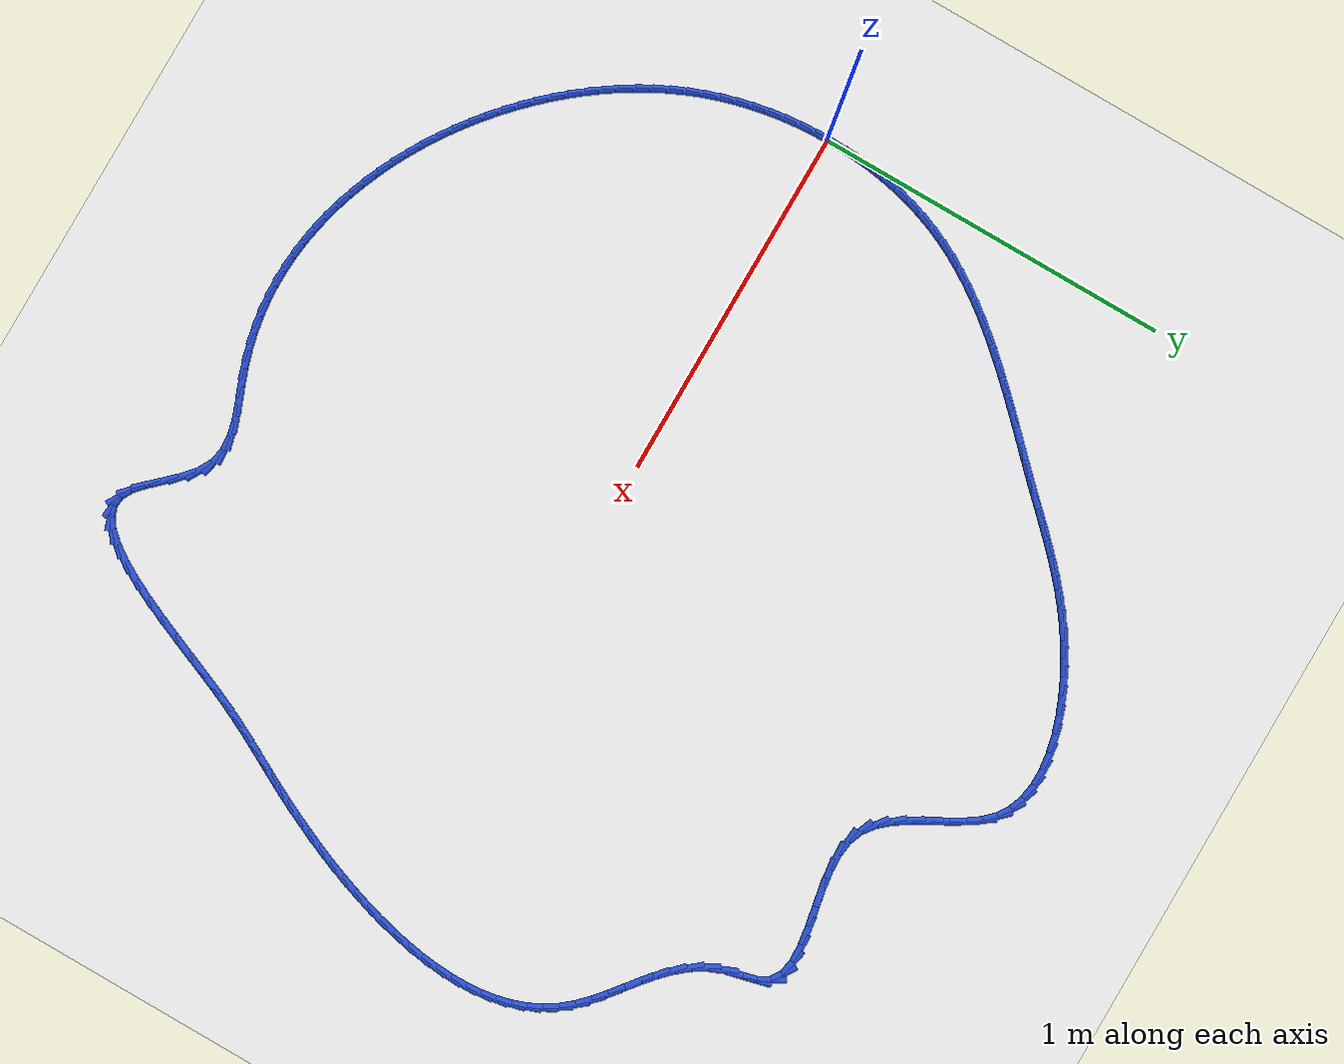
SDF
<sdf version="1.6">
 <world name="default">
  <light name="sun" type="directional">
   <pose>0 0 10 0 -0 0</pose>
   <diffuse>0.8 0.8 0.8 1</diffuse>
   <specular>0.2 0.2 0.2 1</specular>
   <attenuation>
    <range>1000</range>
    <constant>0.9</constant>
    <linear>0.01</linear>
    <quadratic>0.001</quadratic>
   </attenuation>
   <direction>-0.5 0.1 -0.9</direction>
  </light>
  <model name="ground_plane">
   <static>1</static>
   <link name="link">
    <collision name="collision">
     <geometry><plane><normal>0 0 1</normal><size>100 100</size></plane></geometry>
     <surface><friction><ode><mu>100</mu><mu2>50</mu2></ode></friction></surface>
    </collision>
    <visual name="visual">
     <cast_shadows>0</cast_shadows>
     <geometry><plane><normal>0 0 1</normal><size>100 100</size></plane></geometry>
     <material>
      <script><uri>file://media/materials/scripts/gazebo.material</uri><name>Gazebo/WhiteGlow</name></script>
     </material>
    </visual>
   </link>
  </model>
  <gravity>0 0 -9.8</gravity>
  <magnetic_field>6e-06 2.3e-05 -4.2e-05</magnetic_field>
  <atmosphere type="adiabatic"/>
  <physics name="default_physics" default="0" type="ode">
   <max_step_size>0.001</max_step_size>
   <real_time_factor>1</real_time_factor>
   <real_time_update_rate>1000</real_time_update_rate>
  </physics>
  <scene><ambient>0.4 0.4 0.4 1</ambient><background>0.7 0.7 0.7 1</background><shadows>1</shadows></scene>
  <spherical_coordinates>
   <surface_model>EARTH_WGS84</surface_model>
   <latitude_deg>0</latitude_deg>
   <longitude_deg>0</longitude_deg>
   <elevation>0</elevation>
   <heading_deg>0</heading_deg>
  </spherical_coordinates>
  <model name="line">
   <link name="link_0">
    <pose>9.540979117872439e-18 -2.7755575615628914e-17 0.01 0 1.57 1.5550834401233358</pose>
    <collision name="collision">
     <geometry><cylinder><radius>0.01</radius><length>0.08</length></cylinder></geometry>
    </collision>
    <visual name="visual">
     <material>
      <script><name>Gazebo/Blue</name><uri>file://media/materials/scripts/gazebo.material</uri></script>
     </material>
     <geometry><cylinder><radius>0.01</radius><length>0.08</length></cylinder></geometry>
    </visual>
   </link>
   <link name="link_1">
    <pose>0.0007071253182191439 0.04499918677267556 0.01 0 1.57 1.5118088330511579</pose>
    <collision name="collision">
     <geometry><cylinder><radius>0.01</radius><length>0.08</length></cylinder></geometry>
    </collision>
    <visual name="visual">
     <material>
      <script><name>Gazebo/Blue</name><uri>file://media/materials/scripts/gazebo.material</uri></script>
     </material>
     <geometry><cylinder><radius>0.01</radius><length>0.08</length></cylinder></geometry>
    </visual>
   </link>
   <link name="link_2">
    <pose>0.003360584371505938 0.08993041844704301 0.01 0 1.57 1.467205646943557</pose>
    <collision name="collision">
     <geometry><cylinder><radius>0.01</radius><length>0.08</length></cylinder></geometry>
    </collision>
    <visual name="visual">
     <material>
      <script><name>Gazebo/Blue</name><uri>file://media/materials/scripts/gazebo.material</uri></script>
     </material>
     <geometry><cylinder><radius>0.01</radius><length>0.08</length></cylinder></geometry>
    </visual>
   </link>
   <link name="link_3">
    <pose>0.008009777035274087 0.13465018043659344 0.01 0 1.57 1.4210333260894008</pose>
    <collision name="collision">
     <geometry><cylinder><radius>0.01</radius><length>0.08</length></cylinder></geometry>
    </collision>
    <visual name="visual">
     <material>
      <script><name>Gazebo/Blue</name><uri>file://media/materials/scripts/gazebo.material</uri></script>
     </material>
     <geometry><cylinder><radius>0.01</radius><length>0.08</length></cylinder></geometry>
    </visual>
   </link>
   <link name="link_4">
    <pose>0.014704103184937301 0.1790149581548181 0.01 0 1.57 1.3730587600862478</pose>
    <collision name="collision">
     <geometry><cylinder><radius>0.01</radius><length>0.08</length></cylinder></geometry>
    </collision>
    <visual name="visual">
     <material>
      <script><name>Gazebo/Blue</name><uri>file://media/materials/scripts/gazebo.material</uri></script>
     </material>
     <geometry><cylinder><radius>0.01</radius><length>0.08</length></cylinder></geometry>
    </visual>
   </link>
   <link name="link_5">
    <pose>0.023492962695909274 0.22288123701520812 0.01 0 1.57 1.3230601992094901</pose>
    <collision name="collision">
     <geometry><cylinder><radius>0.01</radius><length>0.08</length></cylinder></geometry>
    </collision>
    <visual name="visual">
     <material>
      <script><name>Gazebo/Blue</name><uri>file://media/materials/scripts/gazebo.material</uri></script>
     </material>
     <geometry><cylinder><radius>0.01</radius><length>0.08</length></cylinder></geometry>
    </visual>
   </link>
   <link name="link_6">
    <pose>0.034425755443603705 0.26610550243125464 0.01 0 1.57 1.270833187727479</pose>
    <collision name="collision">
     <geometry><cylinder><radius>0.01</radius><length>0.08</length></cylinder></geometry>
    </collision>
    <visual name="visual">
     <material>
      <script><name>Gazebo/Blue</name><uri>file://media/materials/scripts/gazebo.material</uri></script>
     </material>
     <geometry><cylinder><radius>0.01</radius><length>0.08</length></cylinder></geometry>
    </visual>
   </link>
   <link name="link_7">
    <pose>0.04755188130343429 0.3085442398164489 0.01 0 1.57 1.2161987674992394</pose>
    <collision name="collision">
     <geometry><cylinder><radius>0.01</radius><length>0.08</length></cylinder></geometry>
    </collision>
    <visual name="visual">
     <material>
      <script><name>Gazebo/Blue</name><uri>file://media/materials/scripts/gazebo.material</uri></script>
     </material>
     <geometry><cylinder><radius>0.01</radius><length>0.08</length></cylinder></geometry>
    </visual>
   </link>
   <link name="link_8">
    <pose>0.06292074015081472 0.350053934584282 0.01 0 1.57 1.159440759616084</pose>
    <collision name="collision">
     <geometry><cylinder><radius>0.01</radius><length>0.08</length></cylinder></geometry>
    </collision>
    <visual name="visual">
     <material>
      <script><name>Gazebo/Blue</name><uri>file://media/materials/scripts/gazebo.material</uri></script>
     </material>
     <geometry><cylinder><radius>0.01</radius><length>0.08</length></cylinder></geometry>
    </visual>
   </link>
   <link name="link_9">
    <pose>0.08056701617637128 0.3905044262941944 0.01 0 1.57 1.1045927002458515</pose>
    <collision name="collision">
     <geometry><cylinder><radius>0.01</radius><length>0.08</length></cylinder></geometry>
    </collision>
    <visual name="visual">
     <material>
      <script><name>Gazebo/Blue</name><uri>file://media/materials/scripts/gazebo.material</uri></script>
     </material>
     <geometry><cylinder><radius>0.01</radius><length>0.08</length></cylinder></geometry>
    </visual>
   </link>
   <link name="link_10">
    <pose>0.10038657265252682 0.4298915313004052 0.01 0 1.57 1.0540894822819367</pose>
    <collision name="collision">
     <geometry><cylinder><radius>0.01</radius><length>0.08</length></cylinder></geometry>
    </collision>
    <visual name="visual">
     <material>
      <script><name>Gazebo/Blue</name><uri>file://media/materials/scripts/gazebo.material</uri></script>
     </material>
     <geometry><cylinder><radius>0.01</radius><length>0.08</length></cylinder></geometry>
    </visual>
   </link>
   <link name="link_11">
    <pose>0.12219897173619831 0.46828030746694216 0.01 0 1.57 1.0081014676095499</pose>
    <collision name="collision">
     <geometry><cylinder><radius>0.01</radius><length>0.08</length></cylinder></geometry>
    </collision>
    <visual name="visual">
     <material>
      <script><name>Gazebo/Blue</name><uri>file://media/materials/scripts/gazebo.material</uri></script>
     </material>
     <geometry><cylinder><radius>0.01</radius><length>0.08</length></cylinder></geometry>
    </visual>
   </link>
   <link name="link_12">
    <pose>0.14582298590236115 0.5057365292760575 0.01 0 1.57 0.9666710400697017</pose>
    <collision name="collision">
     <geometry><cylinder><radius>0.01</radius><length>0.08</length></cylinder></geometry>
    </collision>
    <visual name="visual">
     <material>
      <script><name>Gazebo/Blue</name><uri>file://media/materials/scripts/gazebo.material</uri></script>
     </material>
     <geometry><cylinder><radius>0.01</radius><length>0.08</length></cylinder></geometry>
    </visual>
   </link>
   <link name="link_13">
    <pose>0.17107738762599062 0.5423259712100036 0.01 0 1.57 0.9297634189427066</pose>
    <collision name="collision">
     <geometry><cylinder><radius>0.01</radius><length>0.08</length></cylinder></geometry>
    </collision>
    <visual name="visual">
     <material>
      <script><name>Gazebo/Blue</name><uri>file://media/materials/scripts/gazebo.material</uri></script>
     </material>
     <geometry><cylinder><radius>0.01</radius><length>0.08</length></cylinder></geometry>
    </visual>
   </link>
   <link name="link_14">
    <pose>0.19778094938206198 0.5781144077510327 0.01 0 1.57 0.8972928860206639</pose>
    <collision name="collision">
     <geometry><cylinder><radius>0.01</radius><length>0.08</length></cylinder></geometry>
    </collision>
    <visual name="visual">
     <material>
      <script><name>Gazebo/Blue</name><uri>file://media/materials/scripts/gazebo.material</uri></script>
     </material>
     <geometry><cylinder><radius>0.01</radius><length>0.08</length></cylinder></geometry>
    </visual>
   </link>
   <link name="link_15">
    <pose>0.22575244364555064 0.6131676133813969 0.01 0 1.57 0.8691454915981053</pose>
    <collision name="collision">
     <geometry><cylinder><radius>0.01</radius><length>0.08</length></cylinder></geometry>
    </collision>
    <visual name="visual">
     <material>
      <script><name>Gazebo/Blue</name><uri>file://media/materials/scripts/gazebo.material</uri></script>
     </material>
     <geometry><cylinder><radius>0.01</radius><length>0.08</length></cylinder></geometry>
    </visual>
   </link>
   <link name="link_16">
    <pose>0.2548106428914319 0.6475513625833488 0.01 0 1.57 0.8451976060924352</pose>
    <collision name="collision">
     <geometry><cylinder><radius>0.01</radius><length>0.08</length></cylinder></geometry>
    </collision>
    <visual name="visual">
     <material>
      <script><name>Gazebo/Blue</name><uri>file://media/materials/scripts/gazebo.material</uri></script>
     </material>
     <geometry><cylinder><radius>0.01</radius><length>0.08</length></cylinder></geometry>
    </visual>
   </link>
   <link name="link_17">
    <pose>0.2847743195946811 0.6813314298391403 0.01 0 1.57 0.825330462949806</pose>
    <collision name="collision">
     <geometry><cylinder><radius>0.01</radius><length>0.08</length></cylinder></geometry>
    </collision>
    <visual name="visual">
     <material>
      <script><name>Gazebo/Blue</name><uri>file://media/materials/scripts/gazebo.material</uri></script>
     </material>
     <geometry><cylinder><radius>0.01</radius><length>0.08</length></cylinder></geometry>
    </visual>
   </link>
   <link name="link_18">
    <pose>0.3154622462302733 0.7145735896310237 0.01 0 1.57 0.8094412529035325</pose>
    <collision name="collision">
     <geometry><cylinder><radius>0.01</radius><length>0.08</length></cylinder></geometry>
    </collision>
    <visual name="visual">
     <material>
      <script><name>Gazebo/Blue</name><uri>file://media/materials/scripts/gazebo.material</uri></script>
     </material>
     <geometry><cylinder><radius>0.01</radius><length>0.08</length></cylinder></geometry>
    </visual>
   </link>
   <link name="link_19">
    <pose>0.3466931952731842 0.7473436164412515 0.01 0 1.57 0.7974514825935187</pose>
    <collision name="collision">
     <geometry><cylinder><radius>0.01</radius><length>0.08</length></cylinder></geometry>
    </collision>
    <visual name="visual">
     <material>
      <script><name>Gazebo/Blue</name><uri>file://media/materials/scripts/gazebo.material</uri></script>
     </material>
     <geometry><cylinder><radius>0.01</radius><length>0.08</length></cylinder></geometry>
    </visual>
   </link>
   <link name="link_20">
    <pose>0.37828593919838904 0.7797072847520758 0.01 0 1.57 0.7893133020622984</pose>
    <collision name="collision">
     <geometry><cylinder><radius>0.01</radius><length>0.08</length></cylinder></geometry>
    </collision>
    <visual name="visual">
     <material>
      <script><name>Gazebo/Blue</name><uri>file://media/materials/scripts/gazebo.material</uri></script>
     </material>
     <geometry><cylinder><radius>0.01</radius><length>0.08</length></cylinder></geometry>
    </visual>
   </link>
   <link name="link_21">
    <pose>0.410059250480863 0.8117303690457488 0.01 0 1.57 0.7850144102576346</pose>
    <collision name="collision">
     <geometry><cylinder><radius>0.01</radius><length>0.08</length></cylinder></geometry>
    </collision>
    <visual name="visual">
     <material>
      <script><name>Gazebo/Blue</name><uri>file://media/materials/scripts/gazebo.material</uri></script>
     </material>
     <geometry><cylinder><radius>0.01</radius><length>0.08</length></cylinder></geometry>
    </visual>
   </link>
   <link name="link_22">
    <pose>0.4418319015955813 0.8434786438045226 0.01 0 1.57 0.784582010984684</pose>
    <collision name="collision">
     <geometry><cylinder><radius>0.01</radius><length>0.08</length></cylinder></geometry>
    </collision>
    <visual name="visual">
     <material>
      <script><name>Gazebo/Blue</name><uri>file://media/materials/scripts/gazebo.material</uri></script>
     </material>
     <geometry><cylinder><radius>0.01</radius><length>0.08</length></cylinder></geometry>
    </visual>
   </link>
   <link name="link_23">
    <pose>0.4734226650175196 0.8750178835106501 0.01 0 1.57 0.7880861349082375</pose>
    <collision name="collision">
     <geometry><cylinder><radius>0.01</radius><length>0.08</length></cylinder></geometry>
    </collision>
    <visual name="visual">
     <material>
      <script><name>Gazebo/Blue</name><uri>file://media/materials/scripts/gazebo.material</uri></script>
     </material>
     <geometry><cylinder><radius>0.01</radius><length>0.08</length></cylinder></geometry>
    </visual>
   </link>
   <link name="link_24">
    <pose>0.5046503132216529 0.9064138626463831 0.01 0 1.57 0.7952662238021395</pose>
    <collision name="collision">
     <geometry><cylinder><radius>0.01</radius><length>0.08</length></cylinder></geometry>
    </collision>
    <visual name="visual">
     <material>
      <script><name>Gazebo/Blue</name><uri>file://media/materials/scripts/gazebo.material</uri></script>
     </material>
     <geometry><cylinder><radius>0.01</radius><length>0.08</length></cylinder></geometry>
    </visual>
   </link>
   <link name="link_25">
    <pose>0.5353508783307751 0.9377263966275668 0.01 0 1.57 0.8001773195195335</pose>
    <collision name="collision">
     <geometry><cylinder><radius>0.01</radius><length>0.08</length></cylinder></geometry>
    </collision>
    <visual name="visual">
     <material>
      <script><name>Gazebo/Blue</name><uri>file://media/materials/scripts/gazebo.material</uri></script>
     </material>
     <geometry><cylinder><radius>0.01</radius><length>0.08</length></cylinder></geometry>
    </visual>
   </link>
   <link name="link_26">
    <pose>0.5656359662996261 0.9689201562424271 0.01 0 1.57 0.7978334553509787</pose>
    <collision name="collision">
     <geometry><cylinder><radius>0.01</radius><length>0.08</length></cylinder></geometry>
    </collision>
    <visual name="visual">
     <material>
      <script><name>Gazebo/Blue</name><uri>file://media/materials/scripts/gazebo.material</uri></script>
     </material>
     <geometry><cylinder><radius>0.01</radius><length>0.08</length></cylinder></geometry>
    </visual>
   </link>
   <link name="link_27">
    <pose>0.5958385420707335 0.999883385869923 0.01 0 1.57 0.7880096218687553</pose>
    <collision name="collision">
     <geometry><cylinder><radius>0.01</radius><length>0.08</length></cylinder></geometry>
    </collision>
    <visual name="visual">
     <material>
      <script><name>Gazebo/Blue</name><uri>file://media/materials/scripts/gazebo.material</uri></script>
     </material>
     <geometry><cylinder><radius>0.01</radius><length>0.08</length></cylinder></geometry>
    </visual>
   </link>
   <link name="link_28">
    <pose>0.626297823880016 1.0305021708767925 0.01 0 1.57 0.7707823440768787</pose>
    <collision name="collision">
     <geometry><cylinder><radius>0.01</radius><length>0.08</length></cylinder></geometry>
    </collision>
    <visual name="visual">
     <material>
      <script><name>Gazebo/Blue</name><uri>file://media/materials/scripts/gazebo.material</uri></script>
     </material>
     <geometry><cylinder><radius>0.01</radius><length>0.08</length></cylinder></geometry>
    </visual>
   </link>
   <link name="link_29">
    <pose>0.6573530299633915 1.0606625966297727 0.01 0 1.57 0.7464076185970759</pose>
    <collision name="collision">
     <geometry><cylinder><radius>0.01</radius><length>0.08</length></cylinder></geometry>
    </collision>
    <visual name="visual">
     <material>
      <script><name>Gazebo/Blue</name><uri>file://media/materials/scripts/gazebo.material</uri></script>
     </material>
     <geometry><cylinder><radius>0.01</radius><length>0.08</length></cylinder></geometry>
    </visual>
   </link>
   <link name="link_30">
    <pose>0.6893433785567781 1.0902507484956019 0.01 0 1.57 0.7153348200042154</pose>
    <collision name="collision">
     <geometry><cylinder><radius>0.01</radius><length>0.08</length></cylinder></geometry>
    </collision>
    <visual name="visual">
     <material>
      <script><name>Gazebo/Blue</name><uri>file://media/materials/scripts/gazebo.material</uri></script>
     </material>
     <geometry><cylinder><radius>0.01</radius><length>0.08</length></cylinder></geometry>
    </visual>
   </link>
   <link name="link_31">
    <pose>0.7226080878960943 1.1191527118410178 0.01 0 1.57 0.6782142600411807</pose>
    <collision name="collision">
     <geometry><cylinder><radius>0.01</radius><length>0.08</length></cylinder></geometry>
    </collision>
    <visual name="visual">
     <material>
      <script><name>Gazebo/Blue</name><uri>file://media/materials/scripts/gazebo.material</uri></script>
     </material>
     <geometry><cylinder><radius>0.01</radius><length>0.08</length></cylinder></geometry>
    </visual>
   </link>
   <link name="link_32">
    <pose>0.7574863762172586 1.1472545720327583 0.01 0 1.57 0.63589103589535</pose>
    <collision name="collision">
     <geometry><cylinder><radius>0.01</radius><length>0.08</length></cylinder></geometry>
    </collision>
    <visual name="visual">
     <material>
      <script><name>Gazebo/Blue</name><uri>file://media/materials/scripts/gazebo.material</uri></script>
     </material>
     <geometry><cylinder><radius>0.01</radius><length>0.08</length></cylinder></geometry>
    </visual>
   </link>
   <link name="link_33">
    <pose>0.7943174617561888 1.1744424144375614 0.01 0 1.57 0.589378813272113</pose>
    <collision name="collision">
     <geometry><cylinder><radius>0.01</radius><length>0.08</length></cylinder></geometry>
    </collision>
    <visual name="visual">
     <material>
      <script><name>Gazebo/Blue</name><uri>file://media/materials/scripts/gazebo.material</uri></script>
     </material>
     <geometry><cylinder><radius>0.01</radius><length>0.08</length></cylinder></geometry>
    </visual>
   </link>
   <link name="link_34">
    <pose>0.8334405627488032 1.2006023244221642 0.01 0 1.57 0.5398117279089382</pose>
    <collision name="collision">
     <geometry><cylinder><radius>0.01</radius><length>0.08</length></cylinder></geometry>
    </collision>
    <visual name="visual">
     <material>
      <script><name>Gazebo/Blue</name><uri>file://media/materials/scripts/gazebo.material</uri></script>
     </material>
     <geometry><cylinder><radius>0.01</radius><length>0.08</length></cylinder></geometry>
    </visual>
   </link>
   <link name="link_35">
    <pose>0.8751938271506271 1.2256197836267408 0.01 0 1.57 0.4881976379000375</pose>
    <collision name="collision">
     <geometry><cylinder><radius>0.01</radius><length>0.08</length></cylinder></geometry>
    </collision>
    <visual name="visual">
     <material>
      <script><name>Gazebo/Blue</name><uri>file://media/materials/scripts/gazebo.material</uri></script>
     </material>
     <geometry><cylinder><radius>0.01</radius><length>0.08</length></cylinder></geometry>
    </visual>
   </link>
   <link name="link_36">
    <pose>0.9196133794914927 1.2492099075273868 0.01 0 1.57 0.4334016457917671</pose>
    <collision name="collision">
     <geometry><cylinder><radius>0.01</radius><length>0.08</length></cylinder></geometry>
    </collision>
    <visual name="visual">
     <material>
      <script><name>Gazebo/Blue</name><uri>file://media/materials/scripts/gazebo.material</uri></script>
     </material>
     <geometry><cylinder><radius>0.01</radius><length>0.08</length></cylinder></geometry>
    </visual>
   </link>
   <link name="link_37">
    <pose>0.9660202184467447 1.270684421537381 0.01 0 1.57 0.37265274625030415</pose>
    <collision name="collision">
     <geometry><cylinder><radius>0.01</radius><length>0.08</length></cylinder></geometry>
    </collision>
    <visual name="visual">
     <material>
      <script><name>Gazebo/Blue</name><uri>file://media/materials/scripts/gazebo.material</uri></script>
     </material>
     <geometry><cylinder><radius>0.01</radius><length>0.08</length></cylinder></geometry>
    </visual>
   </link>
   <link name="link_38">
    <pose>1.0136318439437413 1.2892966692254786 0.01 0 1.57 0.3027469280048957</pose>
    <collision name="collision">
     <geometry><cylinder><radius>0.01</radius><length>0.08</length></cylinder></geometry>
    </collision>
    <visual name="visual">
     <material>
      <script><name>Gazebo/Blue</name><uri>file://media/materials/scripts/gazebo.material</uri></script>
     </material>
     <geometry><cylinder><radius>0.01</radius><length>0.08</length></cylinder></geometry>
    </visual>
   </link>
   <link name="link_39">
    <pose>1.0616657559098408 1.3042999941604352 0.01 0 1.57 0.21973990278762615</pose>
    <collision name="collision">
     <geometry><cylinder><radius>0.01</radius><length>0.08</length></cylinder></geometry>
    </collision>
    <visual name="visual">
     <material>
      <script><name>Gazebo/Blue</name><uri>file://media/materials/scripts/gazebo.material</uri></script>
     </material>
     <geometry><cylinder><radius>0.01</radius><length>0.08</length></cylinder></geometry>
    </visual>
   </link>
   <link name="link_40">
    <pose>1.1093394542724015 1.3149477399110054 0.01 0 1.57 0.11861937313041776</pose>
    <collision name="collision">
     <geometry><cylinder><radius>0.01</radius><length>0.08</length></cylinder></geometry>
    </collision>
    <visual name="visual">
     <material>
      <script><name>Gazebo/Blue</name><uri>file://media/materials/scripts/gazebo.material</uri></script>
     </material>
     <geometry><cylinder><radius>0.01</radius><length>0.08</length></cylinder></geometry>
    </visual>
   </link>
   <link name="link_41">
    <pose>1.155870438958781 1.320493250045944 0.01 0 1.57 -0.006801300092596281</pose>
    <collision name="collision">
     <geometry><cylinder><radius>0.01</radius><length>0.08</length></cylinder></geometry>
    </collision>
    <visual name="visual">
     <material>
      <script><name>Gazebo/Blue</name><uri>file://media/materials/scripts/gazebo.material</uri></script>
     </material>
     <geometry><cylinder><radius>0.01</radius><length>0.08</length></cylinder></geometry>
    </visual>
   </link>
   <link name="link_42">
    <pose>1.2004762098963384 1.320189868134007 0.01 0 1.57 -0.16319552607183252</pose>
    <collision name="collision">
     <geometry><cylinder><radius>0.01</radius><length>0.08</length></cylinder></geometry>
    </collision>
    <visual name="visual">
     <material>
      <script><name>Gazebo/Blue</name><uri>file://media/materials/scripts/gazebo.material</uri></script>
     </material>
     <geometry><cylinder><radius>0.01</radius><length>0.08</length></cylinder></geometry>
    </visual>
   </link>
   <link name="link_43">
    <pose>1.242374267012431 1.3132909377439492 0.01 0 1.57 -0.35507212002220323</pose>
    <collision name="collision">
     <geometry><cylinder><radius>0.01</radius><length>0.08</length></cylinder></geometry>
    </collision>
    <visual name="visual">
     <material>
      <script><name>Gazebo/Blue</name><uri>file://media/materials/scripts/gazebo.material</uri></script>
     </material>
     <geometry><cylinder><radius>0.01</radius><length>0.08</length></cylinder></geometry>
    </visual>
   </link>
   <link name="link_44">
    <pose>1.2807821102344172 1.2990498024445258 0.01 0 1.57 -0.579289478295245</pose>
    <collision name="collision">
     <geometry><cylinder><radius>0.01</radius><length>0.08</length></cylinder></geometry>
    </collision>
    <visual name="visual">
     <material>
      <script><name>Gazebo/Blue</name><uri>file://media/materials/scripts/gazebo.material</uri></script>
     </material>
     <geometry><cylinder><radius>0.01</radius><length>0.08</length></cylinder></geometry>
    </visual>
   </link>
   <link name="link_45">
    <pose>1.314917424493047 1.2767200701862176 0.01 0 1.57 -0.8018398310301932</pose>
    <collision name="collision">
     <geometry><cylinder><radius>0.01</radius><length>0.08</length></cylinder></geometry>
    </collision>
    <visual name="visual">
     <material>
      <script><name>Gazebo/Blue</name><uri>file://media/materials/scripts/gazebo.material</uri></script>
     </material>
     <geometry><cylinder><radius>0.01</radius><length>0.08</length></cylinder></geometry>
    </visual>
   </link>
   <link name="link_46">
    <pose>1.3444494332299732 1.2462006264479748 0.01 0 1.57 -0.955061525291664</pose>
    <collision name="collision">
     <geometry><cylinder><radius>0.01</radius><length>0.08</length></cylinder></geometry>
    </collision>
    <visual name="visual">
     <material>
      <script><name>Gazebo/Blue</name><uri>file://media/materials/scripts/gazebo.material</uri></script>
     </material>
     <geometry><cylinder><radius>0.01</radius><length>0.08</length></cylinder></geometry>
    </visual>
   </link>
   <link name="link_47">
    <pose>1.370469469846823 1.209422643164982 0.01 0 1.57 -1.0402813294921625</pose>
    <collision name="collision">
     <geometry><cylinder><radius>0.01</radius><length>0.08</length></cylinder></geometry>
    </collision>
    <visual name="visual">
     <material>
      <script><name>Gazebo/Blue</name><uri>file://media/materials/scripts/gazebo.material</uri></script>
     </material>
     <geometry><cylinder><radius>0.01</radius><length>0.08</length></cylinder></geometry>
    </visual>
   </link>
   <link name="link_48">
    <pose>1.3943481317520778 1.1687163784716794 0.01 0 1.57 -1.0708519129498313</pose>
    <collision name="collision">
     <geometry><cylinder><radius>0.01</radius><length>0.08</length></cylinder></geometry>
    </collision>
    <visual name="visual">
     <material>
      <script><name>Gazebo/Blue</name><uri>file://media/materials/scripts/gazebo.material</uri></script>
     </material>
     <geometry><cylinder><radius>0.01</radius><length>0.08</length></cylinder></geometry>
    </visual>
   </link>
   <link name="link_49">
    <pose>1.41745601635422 1.126412090502506 0.01 0 1.57 -1.0525165912882224</pose>
    <collision name="collision">
     <geometry><cylinder><radius>0.01</radius><length>0.08</length></cylinder></geometry>
    </collision>
    <visual name="visual">
     <material>
      <script><name>Gazebo/Blue</name><uri>file://media/materials/scripts/gazebo.material</uri></script>
     </material>
     <geometry><cylinder><radius>0.01</radius><length>0.08</length></cylinder></geometry>
    </visual>
   </link>
   <link name="link_50">
    <pose>1.4411637210617294 1.0848400373918987 0.01 0 1.57 -0.9827023643132725</pose>
    <collision name="collision">
     <geometry><cylinder><radius>0.01</radius><length>0.08</length></cylinder></geometry>
    </collision>
    <visual name="visual">
     <material>
      <script><name>Gazebo/Blue</name><uri>file://media/materials/scripts/gazebo.material</uri></script>
     </material>
     <geometry><cylinder><radius>0.01</radius><length>0.08</length></cylinder></geometry>
    </visual>
   </link>
   <link name="link_51">
    <pose>1.4668418432830894 1.0463304772742996 0.01 0 1.57 -0.851249692300802</pose>
    <collision name="collision">
     <geometry><cylinder><radius>0.01</radius><length>0.08</length></cylinder></geometry>
    </collision>
    <visual name="visual">
     <material>
      <script><name>Gazebo/Blue</name><uri>file://media/materials/scripts/gazebo.material</uri></script>
     </material>
     <geometry><cylinder><radius>0.01</radius><length>0.08</length></cylinder></geometry>
    </visual>
   </link>
   <link name="link_52">
    <pose>1.49586098042678 1.0132136682841453 0.01 0 1.57 -0.6453151404989103</pose>
    <collision name="collision">
     <geometry><cylinder><radius>0.01</radius><length>0.08</length></cylinder></geometry>
    </collision>
    <visual name="visual">
     <material>
      <script><name>Gazebo/Blue</name><uri>file://media/materials/scripts/gazebo.material</uri></script>
     </material>
     <geometry><cylinder><radius>0.01</radius><length>0.08</length></cylinder></geometry>
    </visual>
   </link>
   <link name="link_53">
    <pose>1.5295917299012833 0.9878198685558764 0.01 0 1.57 -0.3691657277952403</pose>
    <collision name="collision">
     <geometry><cylinder><radius>0.01</radius><length>0.08</length></cylinder></geometry>
    </collision>
    <visual name="visual">
     <material>
      <script><name>Gazebo/Blue</name><uri>file://media/materials/scripts/gazebo.material</uri></script>
     </material>
     <geometry><cylinder><radius>0.01</radius><length>0.08</length></cylinder></geometry>
    </visual>
   </link>
   <link name="link_54">
    <pose>1.5693721460366301 0.9724286786203823 0.01 0 1.57 -0.11212887094343497</pose>
    <collision name="collision">
     <geometry><cylinder><radius>0.01</radius><length>0.08</length></cylinder></geometry>
    </collision>
    <visual name="visual">
     <material>
      <script><name>Gazebo/Blue</name><uri>file://media/materials/scripts/gazebo.material</uri></script>
     </material>
     <geometry><cylinder><radius>0.01</radius><length>0.08</length></cylinder></geometry>
    </visual>
   </link>
   <link name="link_55">
    <pose>1.615220990094419 0.967266044947333 0.01 0 1.57 0.05124510057745135</pose>
    <collision name="collision">
     <geometry><cylinder><radius>0.01</radius><length>0.08</length></cylinder></geometry>
    </collision>
    <visual name="visual">
     <material>
      <script><name>Gazebo/Blue</name><uri>file://media/materials/scripts/gazebo.material</uri></script>
     </material>
     <geometry><cylinder><radius>0.01</radius><length>0.08</length></cylinder></geometry>
    </visual>
   </link>
   <link name="link_56">
    <pose>1.6654111946066468 0.9698403008038959 0.01 0 1.57 0.1438754948492338</pose>
    <collision name="collision">
     <geometry><cylinder><radius>0.01</radius><length>0.08</length></cylinder></geometry>
    </collision>
    <visual name="visual">
     <material>
      <script><name>Gazebo/Blue</name><uri>file://media/materials/scripts/gazebo.material</uri></script>
     </material>
     <geometry><cylinder><radius>0.01</radius><length>0.08</length></cylinder></geometry>
    </visual>
   </link>
   <link name="link_57">
    <pose>1.7180957378218271 0.9774730547579817 0.01 0 1.57 0.18558589622574742</pose>
    <collision name="collision">
     <geometry><cylinder><radius>0.01</radius><length>0.08</length></cylinder></geometry>
    </collision>
    <visual name="visual">
     <material>
      <script><name>Gazebo/Blue</name><uri>file://media/materials/scripts/gazebo.material</uri></script>
     </material>
     <geometry><cylinder><radius>0.01</radius><length>0.08</length></cylinder></geometry>
    </visual>
   </link>
   <link name="link_58">
    <pose>1.7714275979884766 0.9874859153775016 0.01 0 1.57 0.1842321169352124</pose>
    <collision name="collision">
     <geometry><cylinder><radius>0.01</radius><length>0.08</length></cylinder></geometry>
    </collision>
    <visual name="visual">
     <material>
      <script><name>Gazebo/Blue</name><uri>file://media/materials/scripts/gazebo.material</uri></script>
     </material>
     <geometry><cylinder><radius>0.01</radius><length>0.08</length></cylinder></geometry>
    </visual>
   </link>
   <link name="link_59">
    <pose>1.823559753355109 0.9972004912303671 0.01 0 1.57 0.1364162802884932</pose>
    <collision name="collision">
     <geometry><cylinder><radius>0.01</radius><length>0.08</length></cylinder></geometry>
    </collision>
    <visual name="visual">
     <material>
      <script><name>Gazebo/Blue</name><uri>file://media/materials/scripts/gazebo.material</uri></script>
     </material>
     <geometry><cylinder><radius>0.01</radius><length>0.08</length></cylinder></geometry>
    </visual>
   </link>
   <link name="link_60">
    <pose>1.87264518217024 1.0039383908844899 0.01 0 1.57 0.024498172003528735</pose>
    <collision name="collision">
     <geometry><cylinder><radius>0.01</radius><length>0.08</length></cylinder></geometry>
    </collision>
    <visual name="visual">
     <material>
      <script><name>Gazebo/Blue</name><uri>file://media/materials/scripts/gazebo.material</uri></script>
     </material>
     <geometry><cylinder><radius>0.01</radius><length>0.08</length></cylinder></geometry>
    </visual>
   </link>
   <link name="link_61">
    <pose>1.9168368626823842 1.0050212229077806 0.01 0 1.57 -0.19123757411691705</pose>
    <collision name="collision">
     <geometry><cylinder><radius>0.01</radius><length>0.08</length></cylinder></geometry>
    </collision>
    <visual name="visual">
     <material>
      <script><name>Gazebo/Blue</name><uri>file://media/materials/scripts/gazebo.material</uri></script>
     </material>
     <geometry><cylinder><radius>0.01</radius><length>0.08</length></cylinder></geometry>
    </visual>
   </link>
   <link name="link_62">
    <pose>1.9542877731400556 0.9977705958681506 0.01 0 1.57 -0.5641365989672306</pose>
    <collision name="collision">
     <geometry><cylinder><radius>0.01</radius><length>0.08</length></cylinder></geometry>
    </collision>
    <visual name="visual">
     <material>
      <script><name>Gazebo/Blue</name><uri>file://media/materials/scripts/gazebo.material</uri></script>
     </material>
     <geometry><cylinder><radius>0.01</radius><length>0.08</length></cylinder></geometry>
    </visual>
   </link>
   <link name="link_63">
    <pose>1.9831508917917704 0.9795081183335113 0.01 0 1.57 -1.0422940859451832</pose>
    <collision name="collision">
     <geometry><cylinder><radius>0.01</radius><length>0.08</length></cylinder></geometry>
    </collision>
    <visual name="visual">
     <material>
      <script><name>Gazebo/Blue</name><uri>file://media/materials/scripts/gazebo.material</uri></script>
     </material>
     <geometry><cylinder><radius>0.01</radius><length>0.08</length></cylinder></geometry>
    </visual>
   </link>
   <link name="link_64">
    <pose>2.0017169995100073 0.9477117656679577 0.01 0 1.57 -1.322288002110685</pose>
    <collision name="collision">
     <geometry><cylinder><radius>0.01</radius><length>0.08</length></cylinder></geometry>
    </collision>
    <visual name="visual">
     <material>
      <script><name>Gazebo/Blue</name><uri>file://media/materials/scripts/gazebo.material</uri></script>
     </material>
     <geometry><cylinder><radius>0.01</radius><length>0.08</length></cylinder></geometry>
    </visual>
   </link>
   <link name="link_65">
    <pose>2.012611559870927 0.9047781456051913 0.01 0 1.57 -1.3365317207906346</pose>
    <collision name="collision">
     <geometry><cylinder><radius>0.01</radius><length>0.08</length></cylinder></geometry>
    </collision>
    <visual name="visual">
     <material>
      <script><name>Gazebo/Blue</name><uri>file://media/materials/scripts/gazebo.material</uri></script>
     </material>
     <geometry><cylinder><radius>0.01</radius><length>0.08</length></cylinder></geometry>
    </visual>
   </link>
   <link name="link_66">
    <pose>2.0235618759777227 0.8588930155090523 0.01 0 1.57 -1.1810696576388164</pose>
    <collision name="collision">
     <geometry><cylinder><radius>0.01</radius><length>0.08</length></cylinder></geometry>
    </collision>
    <visual name="visual">
     <material>
      <script><name>Gazebo/Blue</name><uri>file://media/materials/scripts/gazebo.material</uri></script>
     </material>
     <geometry><cylinder><radius>0.01</radius><length>0.08</length></cylinder></geometry>
    </visual>
   </link>
   <link name="link_67">
    <pose>2.0408406805507453 0.8168250490371916 0.01 0 1.57 -1.0103549081098813</pose>
    <collision name="collision">
     <geometry><cylinder><radius>0.01</radius><length>0.08</length></cylinder></geometry>
    </collision>
    <visual name="visual">
     <material>
      <script><name>Gazebo/Blue</name><uri>file://media/materials/scripts/gazebo.material</uri></script>
     </material>
     <geometry><cylinder><radius>0.01</radius><length>0.08</length></cylinder></geometry>
    </visual>
   </link>
   <link name="link_68">
    <pose>2.064503648687051 0.7791190232605067 0.01 0 1.57 -0.872021855829654</pose>
    <collision name="collision">
     <geometry><cylinder><radius>0.01</radius><length>0.08</length></cylinder></geometry>
    </collision>
    <visual name="visual">
     <material>
      <script><name>Gazebo/Blue</name><uri>file://media/materials/scripts/gazebo.material</uri></script>
     </material>
     <geometry><cylinder><radius>0.01</radius><length>0.08</length></cylinder></geometry>
    </visual>
   </link>
   <link name="link_69">
    <pose>2.093224158769332 0.7449358979646594 0.01 0 1.57 -0.7705102090995946</pose>
    <collision name="collision">
     <geometry><cylinder><radius>0.01</radius><length>0.08</length></cylinder></geometry>
    </collision>
    <visual name="visual">
     <material>
      <script><name>Gazebo/Blue</name><uri>file://media/materials/scripts/gazebo.material</uri></script>
     </material>
     <geometry><cylinder><radius>0.01</radius><length>0.08</length></cylinder></geometry>
    </visual>
   </link>
   <link name="link_70">
    <pose>2.1256755891802803 0.7134366329353097 0.01 0 1.57 -0.7049448520628551</pose>
    <collision name="collision">
     <geometry><cylinder><radius>0.01</radius><length>0.08</length></cylinder></geometry>
    </collision>
    <visual name="visual">
     <material>
      <script><name>Gazebo/Blue</name><uri>file://media/materials/scripts/gazebo.material</uri></script>
     </material>
     <geometry><cylinder><radius>0.01</radius><length>0.08</length></cylinder></geometry>
    </visual>
   </link>
   <link name="link_71">
    <pose>2.160531318302586 0.6837821879581183 0.01 0 1.57 -0.6730747426169894</pose>
    <collision name="collision">
     <geometry><cylinder><radius>0.01</radius><length>0.08</length></cylinder></geometry>
    </collision>
    <visual name="visual">
     <material>
      <script><name>Gazebo/Blue</name><uri>file://media/materials/scripts/gazebo.material</uri></script>
     </material>
     <geometry><cylinder><radius>0.01</radius><length>0.08</length></cylinder></geometry>
    </visual>
   </link>
   <link name="link_72">
    <pose>2.196464724518941 0.6551335228187466 0.01 0 1.57 -0.6736182500969977</pose>
    <collision name="collision">
     <geometry><cylinder><radius>0.01</radius><length>0.08</length></cylinder></geometry>
    </collision>
    <visual name="visual">
     <material>
      <script><name>Gazebo/Blue</name><uri>file://media/materials/scripts/gazebo.material</uri></script>
     </material>
     <geometry><cylinder><radius>0.01</radius><length>0.08</length></cylinder></geometry>
    </visual>
   </link>
   <link name="link_73">
    <pose>2.2321491862120353 0.626651597302855 0.01 0 1.57 -0.707239258921154</pose>
    <collision name="collision">
     <geometry><cylinder><radius>0.01</radius><length>0.08</length></cylinder></geometry>
    </collision>
    <visual name="visual">
     <material>
      <script><name>Gazebo/Blue</name><uri>file://media/materials/scripts/gazebo.material</uri></script>
     </material>
     <geometry><cylinder><radius>0.01</radius><length>0.08</length></cylinder></geometry>
    </visual>
   </link>
   <link name="link_74">
    <pose>2.2662580817645623 0.5974973711961041 0.01 0 1.57 -0.7766522899371278</pose>
    <collision name="collision">
     <geometry><cylinder><radius>0.01</radius><length>0.08</length></cylinder></geometry>
    </collision>
    <visual name="visual">
     <material>
      <script><name>Gazebo/Blue</name><uri>file://media/materials/scripts/gazebo.material</uri></script>
     </material>
     <geometry><cylinder><radius>0.01</radius><length>0.08</length></cylinder></geometry>
    </visual>
   </link>
   <link name="link_75">
    <pose>2.297464789559211 0.5668318042841551 0.01 0 1.57 -0.883912416396191</pose>
    <collision name="collision">
     <geometry><cylinder><radius>0.01</radius><length>0.08</length></cylinder></geometry>
    </collision>
    <visual name="visual">
     <material>
      <script><name>Gazebo/Blue</name><uri>file://media/materials/scripts/gazebo.material</uri></script>
     </material>
     <geometry><cylinder><radius>0.01</radius><length>0.08</length></cylinder></geometry>
    </visual>
   </link>
   <link name="link_76">
    <pose>2.3245060985198216 0.5338590543938475 0.01 0 1.57 -1.0062643681936663</pose>
    <collision name="collision">
     <geometry><cylinder><radius>0.01</radius><length>0.08</length></cylinder></geometry>
    </collision>
    <visual name="visual">
     <material>
      <script><name>Gazebo/Blue</name><uri>file://media/materials/scripts/gazebo.material</uri></script>
     </material>
     <geometry><cylinder><radius>0.01</radius><length>0.08</length></cylinder></geometry>
    </visual>
   </link>
   <link name="link_77">
    <pose>2.3469804599535924 0.4983702815514305 0.01 0 1.57 -1.1235366931615218</pose>
    <collision name="collision">
     <geometry><cylinder><radius>0.01</radius><length>0.08</length></cylinder></geometry>
    </collision>
    <visual name="visual">
     <material>
      <script><name>Gazebo/Blue</name><uri>file://media/materials/scripts/gazebo.material</uri></script>
     </material>
     <geometry><cylinder><radius>0.01</radius><length>0.08</length></cylinder></geometry>
    </visual>
   </link>
   <link name="link_78">
    <pose>2.3651077103572464 0.46057996062197365 0.01 0 1.57 -1.2327835713012818</pose>
    <collision name="collision">
     <geometry><cylinder><radius>0.01</radius><length>0.08</length></cylinder></geometry>
    </collision>
    <visual name="visual">
     <material>
      <script><name>Gazebo/Blue</name><uri>file://media/materials/scripts/gazebo.material</uri></script>
     </material>
     <geometry><cylinder><radius>0.01</radius><length>0.08</length></cylinder></geometry>
    </visual>
   </link>
   <link name="link_79">
    <pose>2.379121425588688 0.4207119263258525 0.01 0 1.57 -1.3325223413943446</pose>
    <collision name="collision">
     <geometry><cylinder><radius>0.01</radius><length>0.08</length></cylinder></geometry>
    </collision>
    <visual name="visual">
     <material>
      <script><name>Gazebo/Blue</name><uri>file://media/materials/scripts/gazebo.material</uri></script>
     </material>
     <geometry><cylinder><radius>0.01</radius><length>0.08</length></cylinder></geometry>
    </visual>
   </link>
   <link name="link_80">
    <pose>2.3892551815058205 0.37899001338344374 0.01 0 1.57 -1.422254287748762</pose>
    <collision name="collision">
     <geometry><cylinder><radius>0.01</radius><length>0.08</length></cylinder></geometry>
    </collision>
    <visual name="visual">
     <material>
      <script><name>Gazebo/Blue</name><uri>file://media/materials/scripts/gazebo.material</uri></script>
     </material>
     <geometry><cylinder><radius>0.01</radius><length>0.08</length></cylinder></geometry>
    </visual>
   </link>
   <link name="link_81">
    <pose>2.3957425539665484 0.33563805651512324 0.01 0 1.57 -1.5022112441180147</pose>
    <collision name="collision">
     <geometry><cylinder><radius>0.01</radius><length>0.08</length></cylinder></geometry>
    </collision>
    <visual name="visual">
     <material>
      <script><name>Gazebo/Blue</name><uri>file://media/materials/scripts/gazebo.material</uri></script>
     </material>
     <geometry><cylinder><radius>0.01</radius><length>0.08</length></cylinder></geometry>
    </visual>
   </link>
   <link name="link_82">
    <pose>2.398817118828773 0.29087989044126644 0.01 0 1.57 1.5685180188777363</pose>
    <collision name="collision">
     <geometry><cylinder><radius>0.01</radius><length>0.08</length></cylinder></geometry>
    </collision>
    <visual name="visual">
     <material>
      <script><name>Gazebo/Blue</name><uri>file://media/materials/scripts/gazebo.material</uri></script>
     </material>
     <geometry><cylinder><radius>0.01</radius><length>0.08</length></cylinder></geometry>
    </visual>
   </link>
   <link name="link_83">
    <pose>2.398712451950401 0.24493934988225027 0.01 0 1.57 1.5058476658511162</pose>
    <collision name="collision">
     <geometry><cylinder><radius>0.01</radius><length>0.08</length></cylinder></geometry>
    </collision>
    <visual name="visual">
     <material>
      <script><name>Gazebo/Blue</name><uri>file://media/materials/scripts/gazebo.material</uri></script>
     </material>
     <geometry><cylinder><radius>0.01</radius><length>0.08</length></cylinder></geometry>
    </visual>
   </link>
   <link name="link_84">
    <pose>2.395662129189333 0.19804026955844994 0.01 0 1.57 1.4504083057956008</pose>
    <collision name="collision">
     <geometry><cylinder><radius>0.01</radius><length>0.08</length></cylinder></geometry>
    </collision>
    <visual name="visual">
     <material>
      <script><name>Gazebo/Blue</name><uri>file://media/materials/scripts/gazebo.material</uri></script>
     </material>
     <geometry><cylinder><radius>0.01</radius><length>0.08</length></cylinder></geometry>
    </visual>
   </link>
   <link name="link_85">
    <pose>2.3898997264034754 0.15040648419024233 0.01 0 1.57 1.4012695308824674</pose>
    <collision name="collision">
     <geometry><cylinder><radius>0.01</radius><length>0.08</length></cylinder></geometry>
    </collision>
    <visual name="visual">
     <material>
      <script><name>Gazebo/Blue</name><uri>file://media/materials/scripts/gazebo.material</uri></script>
     </material>
     <geometry><cylinder><radius>0.01</radius><length>0.08</length></cylinder></geometry>
    </visual>
   </link>
   <link name="link_86">
    <pose>2.381658819450729 0.10226182849800317 0.01 0 1.57 1.3575795052030037</pose>
    <collision name="collision">
     <geometry><cylinder><radius>0.01</radius><length>0.08</length></cylinder></geometry>
    </collision>
    <visual name="visual">
     <material>
      <script><name>Gazebo/Blue</name><uri>file://media/materials/scripts/gazebo.material</uri></script>
     </material>
     <geometry><cylinder><radius>0.01</radius><length>0.08</length></cylinder></geometry>
    </visual>
   </link>
   <link name="link_87">
    <pose>2.371172984189 0.05383013720210836 0.01 0 1.57 1.3185827931030292</pose>
    <collision name="collision">
     <geometry><cylinder><radius>0.01</radius><length>0.08</length></cylinder></geometry>
    </collision>
    <visual name="visual">
     <material>
      <script><name>Gazebo/Blue</name><uri>file://media/materials/scripts/gazebo.material</uri></script>
     </material>
     <geometry><cylinder><radius>0.01</radius><length>0.08</length></cylinder></geometry>
    </visual>
   </link>
   <link name="link_88">
    <pose>2.3586757964761906 0.005335245022934011 0.01 0 1.57 1.2836216635699964</pose>
    <collision name="collision">
     <geometry><cylinder><radius>0.01</radius><length>0.08</length></cylinder></geometry>
    </collision>
    <visual name="visual">
     <material>
      <script><name>Gazebo/Blue</name><uri>file://media/materials/scripts/gazebo.material</uri></script>
     </material>
     <geometry><cylinder><radius>0.01</radius><length>0.08</length></cylinder></geometry>
    </visual>
   </link>
   <link name="link_89">
    <pose>2.344400832170204 -0.0429990133191447 0.01 0 1.57 1.252128991660815</pose>
    <collision name="collision">
     <geometry><cylinder><radius>0.01</radius><length>0.08</length></cylinder></geometry>
    </collision>
    <visual name="visual">
     <material>
      <script><name>Gazebo/Blue</name><uri>file://media/materials/scripts/gazebo.material</uri></script>
     </material>
     <geometry><cylinder><radius>0.01</radius><length>0.08</length></cylinder></geometry>
    </visual>
   </link>
   <link name="link_90">
    <pose>2.3285816671289457 -0.09094880310375003 0.01 0 1.57 1.22361754299838</pose>
    <collision name="collision">
     <geometry><cylinder><radius>0.01</radius><length>0.08</length></cylinder></geometry>
    </collision>
    <visual name="visual">
     <material>
      <script><name>Gazebo/Blue</name><uri>file://media/materials/scripts/gazebo.material</uri></script>
     </material>
     <geometry><cylinder><radius>0.01</radius><length>0.08</length></cylinder></geometry>
    </visual>
   </link>
   <link name="link_91">
    <pose>2.311451877210317 -0.13829028961050666 0.01 0 1.57 1.1976682334905395</pose>
    <collision name="collision">
     <geometry><cylinder><radius>0.01</radius><length>0.08</length></cylinder></geometry>
    </collision>
    <visual name="visual">
     <material>
      <script><name>Gazebo/Blue</name><uri>file://media/materials/scripts/gazebo.material</uri></script>
     </material>
     <geometry><cylinder><radius>0.01</radius><length>0.08</length></cylinder></geometry>
    </visual>
   </link>
   <link name="link_92">
    <pose>2.2932450382722225 -0.18479963811903863 0.01 0 1.57 1.1739186129750017</pose>
    <collision name="collision">
     <geometry><cylinder><radius>0.01</radius><length>0.08</length></cylinder></geometry>
    </collision>
    <visual name="visual">
     <material>
      <script><name>Gazebo/Blue</name><uri>file://media/materials/scripts/gazebo.material</uri></script>
     </material>
     <geometry><cylinder><radius>0.01</radius><length>0.08</length></cylinder></geometry>
    </visual>
   </link>
   <link name="link_93">
    <pose>2.2741947261725666 -0.2302530139089699 0.01 0 1.57 1.152052027311546</pose>
    <collision name="collision">
     <geometry><cylinder><radius>0.01</radius><length>0.08</length></cylinder></geometry>
    </collision>
    <visual name="visual">
     <material>
      <script><name>Gazebo/Blue</name><uri>file://media/materials/scripts/gazebo.material</uri></script>
     </material>
     <geometry><cylinder><radius>0.01</radius><length>0.08</length></cylinder></geometry>
    </visual>
   </link>
   <link name="link_94">
    <pose>2.254534516769252 -0.27442658225992533 0.01 0 1.57 1.131787435719408</pose>
    <collision name="collision">
     <geometry><cylinder><radius>0.01</radius><length>0.08</length></cylinder></geometry>
    </collision>
    <visual name="visual">
     <material>
      <script><name>Gazebo/Blue</name><uri>file://media/materials/scripts/gazebo.material</uri></script>
     </material>
     <geometry><cylinder><radius>0.01</radius><length>0.08</length></cylinder></geometry>
    </visual>
   </link>
   <link name="link_95">
    <pose>2.2344979859201826 -0.3170965084515271 0.01 0 1.57 1.1128695308786785</pose>
    <collision name="collision">
     <geometry><cylinder><radius>0.01</radius><length>0.08</length></cylinder></geometry>
    </collision>
    <visual name="visual">
     <material>
      <script><name>Gazebo/Blue</name><uri>file://media/materials/scripts/gazebo.material</uri></script>
     </material>
     <geometry><cylinder><radius>0.01</radius><length>0.08</length></cylinder></geometry>
    </visual>
   </link>
   <link name="link_96">
    <pose>2.214318709483262 -0.35803895776339995 0.01 0 1.57 1.0951727227376198</pose>
    <collision name="collision">
     <geometry><cylinder><radius>0.01</radius><length>0.08</length></cylinder></geometry>
    </collision>
    <visual name="visual">
     <material>
      <script><name>Gazebo/Blue</name><uri>file://media/materials/scripts/gazebo.material</uri></script>
     </material>
     <geometry><cylinder><radius>0.01</radius><length>0.08</length></cylinder></geometry>
    </visual>
   </link>
   <link name="link_97">
    <pose>2.1942235146462377 -0.39705414003828693 0.01 0 1.57 1.0815811158116941</pose>
    <collision name="collision">
     <geometry><cylinder><radius>0.01</radius><length>0.08</length></cylinder></geometry>
    </collision>
    <visual name="visual">
     <material>
      <script><name>Gazebo/Blue</name><uri>file://media/materials/scripts/gazebo.material</uri></script>
     </material>
     <geometry><cylinder><radius>0.01</radius><length>0.08</length></cylinder></geometry>
    </visual>
   </link>
   <link name="link_98">
    <pose>2.17427668631938 -0.4345213804053726 0.01 0 1.57 1.0761063480815933</pose>
    <collision name="collision">
     <geometry><cylinder><radius>0.01</radius><length>0.08</length></cylinder></geometry>
    </collision>
    <visual name="visual">
     <material>
      <script><name>Gazebo/Blue</name><uri>file://media/materials/scripts/gazebo.material</uri></script>
     </material>
     <geometry><cylinder><radius>0.01</radius><length>0.08</length></cylinder></geometry>
    </visual>
   </link>
   <link name="link_99">
    <pose>2.154375791689177 -0.47141399580852 0.01 0 1.57 1.079549148450456</pose>
    <collision name="collision">
     <geometry><cylinder><radius>0.01</radius><length>0.08</length></cylinder></geometry>
    </collision>
    <visual name="visual">
     <material>
      <script><name>Gazebo/Blue</name><uri>file://media/materials/scripts/gazebo.material</uri></script>
     </material>
     <geometry><cylinder><radius>0.01</radius><length>0.08</length></cylinder></geometry>
    </visual>
   </link>
   <link name="link_100">
    <pose>2.1344108140142874 -0.5087323236604061 0.01 0 1.57 1.0914395599258968</pose>
    <collision name="collision">
     <geometry><cylinder><radius>0.01</radius><length>0.08</length></cylinder></geometry>
    </collision>
    <visual name="visual">
     <material>
      <script><name>Gazebo/Blue</name><uri>file://media/materials/scripts/gazebo.material</uri></script>
     </material>
     <geometry><cylinder><radius>0.01</radius><length>0.08</length></cylinder></geometry>
    </visual>
   </link>
   <link name="link_101">
    <pose>2.1142717365533645 -0.5474767013737093 0.01 0 1.57 1.1103052088640963</pose>
    <collision name="collision">
     <geometry><cylinder><radius>0.01</radius><length>0.08</length></cylinder></geometry>
    </collision>
    <visual name="visual">
     <material>
      <script><name>Gazebo/Blue</name><uri>file://media/materials/scripts/gazebo.material</uri></script>
     </material>
     <geometry><cylinder><radius>0.01</radius><length>0.08</length></cylinder></geometry>
    </visual>
   </link>
   <link name="link_102">
    <pose>2.0938485425650675 -0.5886474663611084 0.01 0 1.57 1.1340740611851818</pose>
    <collision name="collision">
     <geometry><cylinder><radius>0.01</radius><length>0.08</length></cylinder></geometry>
    </collision>
    <visual name="visual">
     <material>
      <script><name>Gazebo/Blue</name><uri>file://media/materials/scripts/gazebo.material</uri></script>
     </material>
     <geometry><cylinder><radius>0.01</radius><length>0.08</length></cylinder></geometry>
    </visual>
   </link>
   <link name="link_103">
    <pose>2.07303121530805 -0.6332449560352809 0.01 0 1.57 1.1592076805965748</pose>
    <collision name="collision">
     <geometry><cylinder><radius>0.01</radius><length>0.08</length></cylinder></geometry>
    </collision>
    <visual name="visual">
     <material>
      <script><name>Gazebo/Blue</name><uri>file://media/materials/scripts/gazebo.material</uri></script>
     </material>
     <geometry><cylinder><radius>0.01</radius><length>0.08</length></cylinder></geometry>
    </visual>
   </link>
   <link name="link_104">
    <pose>2.0517171080607213 -0.6820721478011329 0.01 0 1.57 1.175214959926384</pose>
    <collision name="collision">
     <geometry><cylinder><radius>0.01</radius><length>0.08</length></cylinder></geometry>
    </collision>
    <visual name="visual">
     <material>
      <script><name>Gazebo/Blue</name><uri>file://media/materials/scripts/gazebo.material</uri></script>
     </material>
     <geometry><cylinder><radius>0.01</radius><length>0.08</length></cylinder></geometry>
    </visual>
   </link>
   <link name="link_105">
    <pose>2.0298603419196395 -0.7344118471497724 0.01 0 1.57 1.1800782403941363</pose>
    <collision name="collision">
     <geometry><cylinder><radius>0.01</radius><length>0.08</length></cylinder></geometry>
    </collision>
    <visual name="visual">
     <material>
      <script><name>Gazebo/Blue</name><uri>file://media/materials/scripts/gazebo.material</uri></script>
     </material>
     <geometry><cylinder><radius>0.01</radius><length>0.08</length></cylinder></geometry>
    </visual>
   </link>
   <link name="link_106">
    <pose>2.0074414096894606 -0.788840657867224 0.01 0 1.57 1.1752934486480389</pose>
    <collision name="collision">
     <geometry><cylinder><radius>0.01</radius><length>0.08</length></cylinder></geometry>
    </collision>
    <visual name="visual">
     <material>
      <script><name>Gazebo/Blue</name><uri>file://media/materials/scripts/gazebo.material</uri></script>
     </material>
     <geometry><cylinder><radius>0.01</radius><length>0.08</length></cylinder></geometry>
    </visual>
   </link>
   <link name="link_107">
    <pose>1.9844409498078148 -0.8439312838687203 0.01 0 1.57 1.1609520055146196</pose>
    <collision name="collision">
     <geometry><cylinder><radius>0.01</radius><length>0.08</length></cylinder></geometry>
    </collision>
    <visual name="visual">
     <material>
      <script><name>Gazebo/Blue</name><uri>file://media/materials/scripts/gazebo.material</uri></script>
     </material>
     <geometry><cylinder><radius>0.01</radius><length>0.08</length></cylinder></geometry>
    </visual>
   </link>
   <link name="link_108">
    <pose>1.960839600712333 -0.8982564290694939 0.01 0 1.57 1.1358533674712168</pose>
    <collision name="collision">
     <geometry><cylinder><radius>0.01</radius><length>0.08</length></cylinder></geometry>
    </collision>
    <visual name="visual">
     <material>
      <script><name>Gazebo/Blue</name><uri>file://media/materials/scripts/gazebo.material</uri></script>
     </material>
     <geometry><cylinder><radius>0.01</radius><length>0.08</length></cylinder></geometry>
    </visual>
   </link>
   <link name="link_109">
    <pose>1.9366180008406446 -0.9503887973847767 0.01 0 1.57 1.097220659832309</pose>
    <collision name="collision">
     <geometry><cylinder><radius>0.01</radius><length>0.08</length></cylinder></geometry>
    </collision>
    <visual name="visual">
     <material>
      <script><name>Gazebo/Blue</name><uri>file://media/materials/scripts/gazebo.material</uri></script>
     </material>
     <geometry><cylinder><radius>0.01</radius><length>0.08</length></cylinder></geometry>
    </visual>
   </link>
   <link name="link_110">
    <pose>1.9117567886303801 -0.9989010927298025 0.01 0 1.57 1.0398831380043618</pose>
    <collision name="collision">
     <geometry><cylinder><radius>0.01</radius><length>0.08</length></cylinder></geometry>
    </collision>
    <visual name="visual">
     <material>
      <script><name>Gazebo/Blue</name><uri>file://media/materials/scripts/gazebo.material</uri></script>
     </material>
     <geometry><cylinder><radius>0.01</radius><length>0.08</length></cylinder></geometry>
    </visual>
   </link>
   <link name="link_111">
    <pose>1.8862366025191704 -1.0423660190198016 0.01 0 1.57 0.9545518382829045</pose>
    <collision name="collision">
     <geometry><cylinder><radius>0.01</radius><length>0.08</length></cylinder></geometry>
    </collision>
    <visual name="visual">
     <material>
      <script><name>Gazebo/Blue</name><uri>file://media/materials/scripts/gazebo.material</uri></script>
     </material>
     <geometry><cylinder><radius>0.01</radius><length>0.08</length></cylinder></geometry>
    </visual>
   </link>
   <link name="link_112">
    <pose>1.8600380809446448 -1.0793562801700072 0.01 0 1.57 0.8245333058964786</pose>
    <collision name="collision">
     <geometry><cylinder><radius>0.01</radius><length>0.08</length></cylinder></geometry>
    </collision>
    <visual name="visual">
     <material>
      <script><name>Gazebo/Blue</name><uri>file://media/materials/scripts/gazebo.material</uri></script>
     </material>
     <geometry><cylinder><radius>0.01</radius><length>0.08</length></cylinder></geometry>
    </visual>
   </link>
   <link name="link_113">
    <pose>1.833141862344434 -1.1084445800956524 0.01 0 1.57 0.6210948208969689</pose>
    <collision name="collision">
     <geometry><cylinder><radius>0.01</radius><length>0.08</length></cylinder></geometry>
    </collision>
    <visual name="visual">
     <material>
      <script><name>Gazebo/Blue</name><uri>file://media/materials/scripts/gazebo.material</uri></script>
     </material>
     <geometry><cylinder><radius>0.01</radius><length>0.08</length></cylinder></geometry>
    </visual>
   </link>
   <link name="link_114">
    <pose>1.8055285851561684 -1.1282036227119694 0.01 0 1.57 0.3074803152077454</pose>
    <collision name="collision">
     <geometry><cylinder><radius>0.01</radius><length>0.08</length></cylinder></geometry>
    </collision>
    <visual name="visual">
     <material>
      <script><name>Gazebo/Blue</name><uri>file://media/materials/scripts/gazebo.material</uri></script>
     </material>
     <geometry><cylinder><radius>0.01</radius><length>0.08</length></cylinder></geometry>
    </visual>
   </link>
   <link name="link_115">
    <pose>1.7771788878174772 -1.13720611193419 0.01 0 1.57 -0.10887230418914469</pose>
    <collision name="collision">
     <geometry><cylinder><radius>0.01</radius><length>0.08</length></cylinder></geometry>
    </collision>
    <visual name="visual">
     <material>
      <script><name>Gazebo/Blue</name><uri>file://media/materials/scripts/gazebo.material</uri></script>
     </material>
     <geometry><cylinder><radius>0.01</radius><length>0.08</length></cylinder></geometry>
    </visual>
   </link>
   <link name="link_116">
    <pose>1.748073408765992 -1.134024751677547 0.01 0 1.57 -0.5076331139860487</pose>
    <collision name="collision">
     <geometry><cylinder><radius>0.01</radius><length>0.08</length></cylinder></geometry>
    </collision>
    <visual name="visual">
     <material>
      <script><name>Gazebo/Blue</name><uri>file://media/materials/scripts/gazebo.material</uri></script>
     </material>
     <geometry><cylinder><radius>0.01</radius><length>0.08</length></cylinder></geometry>
    </visual>
   </link>
   <link name="link_117">
    <pose>1.7181851686681446 -1.1173992574431226 0.01 0 1.57 -0.7367854710851709</pose>
    <collision name="collision">
     <geometry><cylinder><radius>0.01</radius><length>0.08</length></cylinder></geometry>
    </collision>
    <visual name="visual">
     <material>
      <script><name>Gazebo/Blue</name><uri>file://media/materials/scripts/gazebo.material</uri></script>
     </material>
     <geometry><cylinder><radius>0.01</radius><length>0.08</length></cylinder></geometry>
    </visual>
   </link>
   <link name="link_118">
    <pose>1.6873347503976759 -1.0894113822968092 0.01 0 1.57 -0.8162944459647538</pose>
    <collision name="collision">
     <geometry><cylinder><radius>0.01</radius><length>0.08</length></cylinder></geometry>
    </collision>
    <visual name="visual">
     <material>
      <script><name>Gazebo/Blue</name><uri>file://media/materials/scripts/gazebo.material</uri></script>
     </material>
     <geometry><cylinder><radius>0.01</radius><length>0.08</length></cylinder></geometry>
    </visual>
   </link>
   <link name="link_119">
    <pose>1.6552019692937066 -1.0552290587898774 0.01 0 1.57 -0.8050443434836526</pose>
    <collision name="collision">
     <geometry><cylinder><radius>0.01</radius><length>0.08</length></cylinder></geometry>
    </collision>
    <visual name="visual">
     <material>
      <script><name>Gazebo/Blue</name><uri>file://media/materials/scripts/gazebo.material</uri></script>
     </material>
     <geometry><cylinder><radius>0.01</radius><length>0.08</length></cylinder></geometry>
    </visual>
   </link>
   <link name="link_120">
    <pose>1.621461361618239 -1.0201359576624107 0.01 0 1.57 -0.710925760095772</pose>
    <collision name="collision">
     <geometry><cylinder><radius>0.01</radius><length>0.08</length></cylinder></geometry>
    </collision>
    <visual name="visual">
     <material>
      <script><name>Gazebo/Blue</name><uri>file://media/materials/scripts/gazebo.material</uri></script>
     </material>
     <geometry><cylinder><radius>0.01</radius><length>0.08</length></cylinder></geometry>
    </visual>
   </link>
   <link name="link_121">
    <pose>1.5857874636332754 -0.9894157496544939 0.01 0 1.57 -0.5069071161262191</pose>
    <collision name="collision">
     <geometry><cylinder><radius>0.01</radius><length>0.08</length></cylinder></geometry>
    </collision>
    <visual name="visual">
     <material>
      <script><name>Gazebo/Blue</name><uri>file://media/materials/scripts/gazebo.material</uri></script>
     </material>
     <geometry><cylinder><radius>0.01</radius><length>0.08</length></cylinder></geometry>
    </visual>
   </link>
   <link name="link_122">
    <pose>1.547854862654067 -0.9683515819845179 0.01 0 1.57 -0.1922941177773128</pose>
    <collision name="collision">
     <geometry><cylinder><radius>0.01</radius><length>0.08</length></cylinder></geometry>
    </collision>
    <visual name="visual">
     <material>
      <script><name>Gazebo/Blue</name><uri>file://media/materials/scripts/gazebo.material</uri></script>
     </material>
     <geometry><cylinder><radius>0.01</radius><length>0.08</length></cylinder></geometry>
    </visual>
   </link>
   <link name="link_123">
    <pose>1.5075069274967796 -0.9604958445800025 0.01 0 1.57 0.07817731863065544</pose>
    <collision name="collision">
     <geometry><cylinder><radius>0.01</radius><length>0.08</length></cylinder></geometry>
    </collision>
    <visual name="visual">
     <material>
      <script><name>Gazebo/Blue</name><uri>file://media/materials/scripts/gazebo.material</uri></script>
     </material>
     <geometry><cylinder><radius>0.01</radius><length>0.08</length></cylinder></geometry>
    </visual>
   </link>
   <link name="link_124">
    <pose>1.4651317222945277 -0.9638153899370432 0.01 0 1.57 0.25269919657112283</pose>
    <collision name="collision">
     <geometry><cylinder><radius>0.01</radius><length>0.08</length></cylinder></geometry>
    </collision>
    <visual name="visual">
     <material>
      <script><name>Gazebo/Blue</name><uri>file://media/materials/scripts/gazebo.material</uri></script>
     </material>
     <geometry><cylinder><radius>0.01</radius><length>0.08</length></cylinder></geometry>
    </visual>
   </link>
   <link name="link_125">
    <pose>1.4212269847136811 -0.9751524314990997 0.01 0 1.57 0.3459416472000235</pose>
    <collision name="collision">
     <geometry><cylinder><radius>0.01</radius><length>0.08</length></cylinder></geometry>
    </collision>
    <visual name="visual">
     <material>
      <script><name>Gazebo/Blue</name><uri>file://media/materials/scripts/gazebo.material</uri></script>
     </material>
     <geometry><cylinder><radius>0.01</radius><length>0.08</length></cylinder></geometry>
    </visual>
   </link>
   <link name="link_126">
    <pose>1.376290452420607 -0.9913491827096295 0.01 0 1.57 0.3750046065148913</pose>
    <collision name="collision">
     <geometry><cylinder><radius>0.01</radius><length>0.08</length></cylinder></geometry>
    </collision>
    <visual name="visual">
     <material>
      <script><name>Gazebo/Blue</name><uri>file://media/materials/scripts/gazebo.material</uri></script>
     </material>
     <geometry><cylinder><radius>0.01</radius><length>0.08</length></cylinder></geometry>
    </visual>
   </link>
   <link name="link_127">
    <pose>1.3308198630816765 -1.009247857012092 0.01 0 1.57 0.34781542419087935</pose>
    <collision name="collision">
     <geometry><cylinder><radius>0.01</radius><length>0.08</length></cylinder></geometry>
    </collision>
    <visual name="visual">
     <material>
      <script><name>Gazebo/Blue</name><uri>file://media/materials/scripts/gazebo.material</uri></script>
     </material>
     <geometry><cylinder><radius>0.01</radius><length>0.08</length></cylinder></geometry>
    </visual>
   </link>
   <link name="link_128">
    <pose>1.285304015192878 -1.025749846237337 0.01 0 1.57 0.2900699863198498</pose>
    <collision name="collision">
     <geometry><cylinder><radius>0.01</radius><length>0.08</length></cylinder></geometry>
    </collision>
    <visual name="visual">
     <material>
      <script><name>Gazebo/Blue</name><uri>file://media/materials/scripts/gazebo.material</uri></script>
     </material>
     <geometry><cylinder><radius>0.01</radius><length>0.08</length></cylinder></geometry>
    </visual>
   </link>
   <link name="link_129">
    <pose>1.2400028276651585 -1.039271752708278 0.01 0 1.57 0.2302499941510786</pose>
    <collision name="collision">
     <geometry><cylinder><radius>0.01</radius><length>0.08</length></cylinder></geometry>
    </collision>
    <visual name="visual">
     <material>
      <script><name>Gazebo/Blue</name><uri>file://media/materials/scripts/gazebo.material</uri></script>
     </material>
     <geometry><cylinder><radius>0.01</radius><length>0.08</length></cylinder></geometry>
    </visual>
   </link>
   <link name="link_130">
    <pose>1.1949336078128656 -1.0498362968146573 0.01 0 1.57 0.17025188518578221</pose>
    <collision name="collision">
     <geometry><cylinder><radius>0.01</radius><length>0.08</length></cylinder></geometry>
    </collision>
    <visual name="visual">
     <material>
      <script><name>Gazebo/Blue</name><uri>file://media/materials/scripts/gazebo.material</uri></script>
     </material>
     <geometry><cylinder><radius>0.01</radius><length>0.08</length></cylinder></geometry>
    </visual>
   </link>
   <link name="link_131">
    <pose>1.150101974454506 -1.0575435782001659 0.01 0 1.57 0.11056524913342555</pose>
    <collision name="collision">
     <geometry><cylinder><radius>0.01</radius><length>0.08</length></cylinder></geometry>
    </collision>
    <visual name="visual">
     <material>
      <script><name>Gazebo/Blue</name><uri>file://media/materials/scripts/gazebo.material</uri></script>
     </material>
     <geometry><cylinder><radius>0.01</radius><length>0.08</length></cylinder></geometry>
    </visual>
   </link>
   <link name="link_132">
    <pose>1.1055135464085863 -1.0624936965084941 0.01 0 1.57 0.05166969651844424</pose>
    <collision name="collision">
     <geometry><cylinder><radius>0.01</radius><length>0.08</length></cylinder></geometry>
    </collision>
    <visual name="visual">
     <material>
      <script><name>Gazebo/Blue</name><uri>file://media/materials/scripts/gazebo.material</uri></script>
     </material>
     <geometry><cylinder><radius>0.01</radius><length>0.08</length></cylinder></geometry>
    </visual>
   </link>
   <link name="link_133">
    <pose>1.0611739424936135 -1.0647867513833336 0.01 0 1.57 -0.00598627195045169</pose>
    <collision name="collision">
     <geometry><cylinder><radius>0.01</radius><length>0.08</length></cylinder></geometry>
    </collision>
    <visual name="visual">
     <material>
      <script><name>Gazebo/Blue</name><uri>file://media/materials/scripts/gazebo.material</uri></script>
     </material>
     <geometry><cylinder><radius>0.01</radius><length>0.08</length></cylinder></geometry>
    </visual>
   </link>
   <link name="link_134">
    <pose>1.0170887815280936 -1.0645228424683753 0.01 0 1.57 -0.06200295418543772</pose>
    <collision name="collision">
     <geometry><cylinder><radius>0.01</radius><length>0.08</length></cylinder></geometry>
    </collision>
    <visual name="visual">
     <material>
      <script><name>Gazebo/Blue</name><uri>file://media/materials/scripts/gazebo.material</uri></script>
     </material>
     <geometry><cylinder><radius>0.01</radius><length>0.08</length></cylinder></geometry>
    </visual>
   </link>
   <link name="link_135">
    <pose>0.9732636823305332 -1.0618020694073107 0.01 0 1.57 -0.11604209281798042</pose>
    <collision name="collision">
     <geometry><cylinder><radius>0.01</radius><length>0.08</length></cylinder></geometry>
    </collision>
    <visual name="visual">
     <material>
      <script><name>Gazebo/Blue</name><uri>file://media/materials/scripts/gazebo.material</uri></script>
     </material>
     <geometry><cylinder><radius>0.01</radius><length>0.08</length></cylinder></geometry>
    </visual>
   </link>
   <link name="link_136">
    <pose>0.9297042637194378 -1.05672453184383 0.01 0 1.57 -0.16783378851136307</pose>
    <collision name="collision">
     <geometry><cylinder><radius>0.01</radius><length>0.08</length></cylinder></geometry>
    </collision>
    <visual name="visual">
     <material>
      <script><name>Gazebo/Blue</name><uri>file://media/materials/scripts/gazebo.material</uri></script>
     </material>
     <geometry><cylinder><radius>0.01</radius><length>0.08</length></cylinder></geometry>
    </visual>
   </link>
   <link name="link_137">
    <pose>0.8864161445133155 -1.0493903294216247 0.01 0 1.57 -0.2172127889429104</pose>
    <collision name="collision">
     <geometry><cylinder><radius>0.01</radius><length>0.08</length></cylinder></geometry>
    </collision>
    <visual name="visual">
     <material>
      <script><name>Gazebo/Blue</name><uri>file://media/materials/scripts/gazebo.material</uri></script>
     </material>
     <geometry><cylinder><radius>0.01</radius><length>0.08</length></cylinder></geometry>
    </visual>
   </link>
   <link name="link_138">
    <pose>0.8434072776040783 -1.0398985026121863 0.01 0 1.57 -0.2645844963397612</pose>
    <collision name="collision">
     <geometry><cylinder><radius>0.01</radius><length>0.08</length></cylinder></geometry>
    </collision>
    <visual name="visual">
     <material>
      <script><name>Gazebo/Blue</name><uri>file://media/materials/scripts/gazebo.material</uri></script>
     </material>
     <geometry><cylinder><radius>0.01</radius><length>0.08</length></cylinder></geometry>
    </visual>
   </link>
   <link name="link_139">
    <pose>0.800719348427887 -1.0283327844964982 0.01 0 1.57 -0.3103763805216823</pose>
    <collision name="collision">
     <geometry><cylinder><radius>0.01</radius><length>0.08</length></cylinder></geometry>
    </collision>
    <visual name="visual">
     <material>
      <script><name>Gazebo/Blue</name><uri>file://media/materials/scripts/gazebo.material</uri></script>
     </material>
     <geometry><cylinder><radius>0.01</radius><length>0.08</length></cylinder></geometry>
    </visual>
   </link>
   <link name="link_140">
    <pose>0.7584194132913415 -1.0147653951840212 0.01 0 1.57 -0.354689788335446</pose>
    <collision name="collision">
     <geometry><cylinder><radius>0.01</radius><length>0.08</length></cylinder></geometry>
    </collision>
    <visual name="visual">
     <material>
      <script><name>Gazebo/Blue</name><uri>file://media/materials/scripts/gazebo.material</uri></script>
     </material>
     <geometry><cylinder><radius>0.01</radius><length>0.08</length></cylinder></geometry>
    </visual>
   </link>
   <link name="link_141">
    <pose>0.7165751475841282 -0.9992682738523517 0.01 0 1.57 -0.3976306123874729</pose>
    <collision name="collision">
     <geometry><cylinder><radius>0.01</radius><length>0.08</length></cylinder></geometry>
    </collision>
    <visual name="visual">
     <material>
      <script><name>Gazebo/Blue</name><uri>file://media/materials/scripts/gazebo.material</uri></script>
     </material>
     <geometry><cylinder><radius>0.01</radius><length>0.08</length></cylinder></geometry>
    </visual>
   </link>
   <link name="link_142">
    <pose>0.6752542266959327 -0.981913359679085 0.01 0 1.57 -0.4393149258305776</pose>
    <collision name="collision">
     <geometry><cylinder><radius>0.01</radius><length>0.08</length></cylinder></geometry>
    </collision>
    <visual name="visual">
     <material>
      <script><name>Gazebo/Blue</name><uri>file://media/materials/scripts/gazebo.material</uri></script>
     </material>
     <geometry><cylinder><radius>0.01</radius><length>0.08</length></cylinder></geometry>
    </visual>
   </link>
   <link name="link_143">
    <pose>0.6345243260164426 -0.9627725918418181 0.01 0 1.57 -0.4798660554002749</pose>
    <collision name="collision">
     <geometry><cylinder><radius>0.01</radius><length>0.08</length></cylinder></geometry>
    </collision>
    <visual name="visual">
     <material>
      <script><name>Gazebo/Blue</name><uri>file://media/materials/scripts/gazebo.material</uri></script>
     </material>
     <geometry><cylinder><radius>0.01</radius><length>0.08</length></cylinder></geometry>
    </visual>
   </link>
   <link name="link_144">
    <pose>0.5944531209353435 -0.9419179095181467 0.01 0 1.57 -0.5194123072626243</pose>
    <collision name="collision">
     <geometry><cylinder><radius>0.01</radius><length>0.08</length></cylinder></geometry>
    </collision>
    <visual name="visual">
     <material>
      <script><name>Gazebo/Blue</name><uri>file://media/materials/scripts/gazebo.material</uri></script>
     </material>
     <geometry><cylinder><radius>0.01</radius><length>0.08</length></cylinder></geometry>
    </visual>
   </link>
   <link name="link_145">
    <pose>0.5551082868423219 -0.9194212518856667 0.01 0 1.57 -0.5580852775460803</pose>
    <collision name="collision">
     <geometry><cylinder><radius>0.01</radius><length>0.08</length></cylinder></geometry>
    </collision>
    <visual name="visual">
     <material>
      <script><name>Gazebo/Blue</name><uri>file://media/materials/scripts/gazebo.material</uri></script>
     </material>
     <geometry><cylinder><radius>0.01</radius><length>0.08</length></cylinder></geometry>
    </visual>
   </link>
   <link name="link_146">
    <pose>0.5165574991270642 -0.8953545581219747 0.01 0 1.57 -0.5960186685964389</pose>
    <collision name="collision">
     <geometry><cylinder><radius>0.01</radius><length>0.08</length></cylinder></geometry>
    </collision>
    <visual name="visual">
     <material>
      <script><name>Gazebo/Blue</name><uri>file://media/materials/scripts/gazebo.material</uri></script>
     </material>
     <geometry><cylinder><radius>0.01</radius><length>0.08</length></cylinder></geometry>
    </visual>
   </link>
   <link name="link_147">
    <pose>0.4788684331792553 -0.8697897674046655 0.01 0 1.57 -0.6333475304598913</pose>
    <collision name="collision">
     <geometry><cylinder><radius>0.01</radius><length>0.08</length></cylinder></geometry>
    </collision>
    <visual name="visual">
     <material>
      <script><name>Gazebo/Blue</name><uri>file://media/materials/scripts/gazebo.material</uri></script>
     </material>
     <geometry><cylinder><radius>0.01</radius><length>0.08</length></cylinder></geometry>
    </visual>
   </link>
   <link name="link_148">
    <pose>0.44210876438858354 -0.8427988189113368 0.01 0 1.57 -0.6702078510841295</pose>
    <collision name="collision">
     <geometry><cylinder><radius>0.01</radius><length>0.08</length></cylinder></geometry>
    </collision>
    <visual name="visual">
     <material>
      <script><name>Gazebo/Blue</name><uri>file://media/materials/scripts/gazebo.material</uri></script>
     </material>
     <geometry><cylinder><radius>0.01</radius><length>0.08</length></cylinder></geometry>
    </visual>
   </link>
   <link name="link_149">
    <pose>0.4063461681447343 -0.814453651819584 0.01 0 1.57 -0.7067364253834683</pose>
    <collision name="collision">
     <geometry><cylinder><radius>0.01</radius><length>0.08</length></cylinder></geometry>
    </collision>
    <visual name="visual">
     <material>
      <script><name>Gazebo/Blue</name><uri>file://media/materials/scripts/gazebo.material</uri></script>
     </material>
     <geometry><cylinder><radius>0.01</radius><length>0.08</length></cylinder></geometry>
    </visual>
   </link>
   <link name="link_150">
    <pose>0.3716483198373938 -0.7848262053070031 0.01 0 1.57 -0.7430709406189794</pose>
    <collision name="collision">
     <geometry><cylinder><radius>0.01</radius><length>0.08</length></cylinder></geometry>
    </collision>
    <visual name="visual">
     <material>
      <script><name>Gazebo/Blue</name><uri>file://media/materials/scripts/gazebo.material</uri></script>
     </material>
     <geometry><cylinder><radius>0.01</radius><length>0.08</length></cylinder></geometry>
    </visual>
   </link>
   <link name="link_151">
    <pose>0.3380828948562485 -0.7539884185511903 0.01 0 1.57 -0.7793502221149875</pose>
    <collision name="collision">
     <geometry><cylinder><radius>0.01</radius><length>0.08</length></cylinder></geometry>
    </collision>
    <visual name="visual">
     <material>
      <script><name>Gazebo/Blue</name><uri>file://media/materials/scripts/gazebo.material</uri></script>
     </material>
     <geometry><cylinder><radius>0.01</radius><length>0.08</length></cylinder></geometry>
    </visual>
   </link>
   <link name="link_152">
    <pose>0.3057175685909845 -0.7220122307297415 0.01 0 1.57 -0.8157145882430757</pose>
    <collision name="collision">
     <geometry><cylinder><radius>0.01</radius><length>0.08</length></cylinder></geometry>
    </collision>
    <visual name="visual">
     <material>
      <script><name>Gazebo/Blue</name><uri>file://media/materials/scripts/gazebo.material</uri></script>
     </material>
     <geometry><cylinder><radius>0.01</radius><length>0.08</length></cylinder></geometry>
    </visual>
   </link>
   <link name="link_153">
    <pose>0.27462001643128764 -0.6889695810202523 0.01 0 1.57 -0.8523285863948651</pose>
    <collision name="collision">
     <geometry><cylinder><radius>0.01</radius><length>0.08</length></cylinder></geometry>
    </collision>
    <visual name="visual">
     <material>
      <script><name>Gazebo/Blue</name><uri>file://media/materials/scripts/gazebo.material</uri></script>
     </material>
     <geometry><cylinder><radius>0.01</radius><length>0.08</length></cylinder></geometry>
    </visual>
   </link>
   <link name="link_154">
    <pose>0.24485797236484633 -0.6549309424417827 0.01 0 1.57 -0.8897337396380558</pose>
    <collision name="collision">
     <geometry><cylinder><radius>0.01</radius><length>0.08</length></cylinder></geometry>
    </collision>
    <visual name="visual">
     <material>
      <script><name>Gazebo/Blue</name><uri>file://media/materials/scripts/gazebo.material</uri></script>
     </material>
     <geometry><cylinder><radius>0.01</radius><length>0.08</length></cylinder></geometry>
    </visual>
   </link>
   <link name="link_155">
    <pose>0.21650025793792255 -0.6199395766193836 0.01 0 1.57 -0.9283656251054418</pose>
    <collision name="collision">
     <geometry><cylinder><radius>0.01</radius><length>0.08</length></cylinder></geometry>
    </collision>
    <visual name="visual">
     <material>
      <script><name>Gazebo/Blue</name><uri>file://media/materials/scripts/gazebo.material</uri></script>
     </material>
     <geometry><cylinder><radius>0.01</radius><length>0.08</length></cylinder></geometry>
    </visual>
   </link>
   <link name="link_156">
    <pose>0.18961665476516218 -0.5840147236682474 0.01 0 1.57 -0.9682836092752466</pose>
    <collision name="collision">
     <geometry><cylinder><radius>0.01</radius><length>0.08</length></cylinder></geometry>
    </collision>
    <visual name="visual">
     <material>
      <script><name>Gazebo/Blue</name><uri>file://media/materials/scripts/gazebo.material</uri></script>
     </material>
     <geometry><cylinder><radius>0.01</radius><length>0.08</length></cylinder></geometry>
    </visual>
   </link>
   <link name="link_157">
    <pose>0.16427697743684322 -0.5471747986326763 0.01 0 1.57 -1.0095227609310535</pose>
    <collision name="collision">
     <geometry><cylinder><radius>0.01</radius><length>0.08</length></cylinder></geometry>
    </collision>
    <visual name="visual">
     <material>
      <script><name>Gazebo/Blue</name><uri>file://media/materials/scripts/gazebo.material</uri></script>
     </material>
     <geometry><cylinder><radius>0.01</radius><length>0.08</length></cylinder></geometry>
    </visual>
   </link>
   <link name="link_158">
    <pose>0.1405510405432432 -0.5094382165569709 0.01 0 1.57 -1.0521038675251917</pose>
    <collision name="collision">
     <geometry><cylinder><radius>0.01</radius><length>0.08</length></cylinder></geometry>
    </collision>
    <visual name="visual">
     <material>
      <script><name>Gazebo/Blue</name><uri>file://media/materials/scripts/gazebo.material</uri></script>
     </material>
     <geometry><cylinder><radius>0.01</radius><length>0.08</length></cylinder></geometry>
    </visual>
   </link>
   <link name="link_159">
    <pose>0.11850865867464107 -0.47082339248543426 0.01 0 1.57 -1.0960307536422815</pose>
    <collision name="collision">
     <geometry><cylinder><radius>0.01</radius><length>0.08</length></cylinder></geometry>
    </collision>
    <visual name="visual">
     <material>
      <script><name>Gazebo/Blue</name><uri>file://media/materials/scripts/gazebo.material</uri></script>
     </material>
     <geometry><cylinder><radius>0.01</radius><length>0.08</length></cylinder></geometry>
    </visual>
   </link>
   <link name="link_160">
    <pose>0.09821964642131446 -0.43134874146236735 0.01 0 1.57 -1.1412875854462197</pose>
    <collision name="collision">
     <geometry><cylinder><radius>0.01</radius><length>0.08</length></cylinder></geometry>
    </collision>
    <visual name="visual">
     <material>
      <script><name>Gazebo/Blue</name><uri>file://media/materials/scripts/gazebo.material</uri></script>
     </material>
     <geometry><cylinder><radius>0.01</radius><length>0.08</length></cylinder></geometry>
    </visual>
   </link>
   <link name="link_161">
    <pose>0.07975381837354137 -0.3910326785320716 0.01 0 1.57 -1.187828895075791</pose>
    <collision name="collision">
     <geometry><cylinder><radius>0.01</radius><length>0.08</length></cylinder></geometry>
    </collision>
    <visual name="visual">
     <material>
      <script><name>Gazebo/Blue</name><uri>file://media/materials/scripts/gazebo.material</uri></script>
     </material>
     <geometry><cylinder><radius>0.01</radius><length>0.08</length></cylinder></geometry>
    </visual>
   </link>
   <link name="link_162">
    <pose>0.06318073072175871 -0.3498938594701129 0.01 0 1.57 -1.2348893807966823</pose>
    <collision name="collision">
     <geometry><cylinder><radius>0.01</radius><length>0.08</length></cylinder></geometry>
    </collision>
    <visual name="visual">
     <material>
      <script><name>Gazebo/Blue</name><uri>file://media/materials/scripts/gazebo.material</uri></script>
     </material>
     <geometry><cylinder><radius>0.01</radius><length>0.08</length></cylinder></geometry>
    </visual>
   </link>
   <link name="link_163">
    <pose>0.048544972394158316 -0.3079742001305943 0.01 0 1.57 -1.2811836321601968</pose>
    <collision name="collision">
     <geometry><cylinder><radius>0.01</radius><length>0.08</length></cylinder></geometry>
    </collision>
    <visual name="visual">
     <material>
      <script><name>Gazebo/Blue</name><uri>file://media/materials/scripts/gazebo.material</uri></script>
     </material>
     <geometry><cylinder><radius>0.01</radius><length>0.08</length></cylinder></geometry>
    </visual>
   </link>
   <link name="link_164">
    <pose>0.03584570731764877 -0.2653579353486583 0.01 0 1.57 -1.326636854341042</pose>
    <collision name="collision">
     <geometry><cylinder><radius>0.01</radius><length>0.08</length></cylinder></geometry>
    </collision>
    <visual name="visual">
     <material>
      <script><name>Gazebo/Blue</name><uri>file://media/materials/scripts/gazebo.material</uri></script>
     </material>
     <geometry><cylinder><radius>0.01</radius><length>0.08</length></cylinder></geometry>
    </visual>
   </link>
   <link name="link_165">
    <pose>0.02507728415059596 -0.22213378597490677 0.01 0 1.57 -1.3713228550975172</pose>
    <collision name="collision">
     <geometry><cylinder><radius>0.01</radius><length>0.08</length></cylinder></geometry>
    </collision>
    <visual name="visual">
     <material>
      <script><name>Gazebo/Blue</name><uri>file://media/materials/scripts/gazebo.material</uri></script>
     </material>
     <geometry><cylinder><radius>0.01</radius><length>0.08</length></cylinder></geometry>
    </visual>
   </link>
   <link name="link_166">
    <pose>0.016234051551366094 -0.17839047285994197 0.01 0 1.57 -1.4153235332090688</pose>
    <collision name="collision">
     <geometry><cylinder><radius>0.01</radius><length>0.08</length></cylinder></geometry>
    </collision>
    <visual name="visual">
     <material>
      <script><name>Gazebo/Blue</name><uri>file://media/materials/scripts/gazebo.material</uri></script>
     </material>
     <geometry><cylinder><radius>0.01</radius><length>0.08</length></cylinder></geometry>
    </visual>
   </link>
   <link name="link_167">
    <pose>0.009310358178325368 -0.13421671685436648 0.01 0 1.57 -1.458727119352608</pose>
    <collision name="collision">
     <geometry><cylinder><radius>0.01</radius><length>0.08</length></cylinder></geometry>
    </collision>
    <visual name="visual">
     <material>
      <script><name>Gazebo/Blue</name><uri>file://media/materials/scripts/gazebo.material</uri></script>
     </material>
     <geometry><cylinder><radius>0.01</radius><length>0.08</length></cylinder></geometry>
    </visual>
   </link>
   <link name="link_168">
    <pose>0.0043005526898399 -0.08970123880878199 0.01 0 1.57 -1.501626656679884</pose>
    <collision name="collision">
     <geometry><cylinder><radius>0.01</radius><length>0.08</length></cylinder></geometry>
    </collision>
    <visual name="visual">
     <material>
      <script><name>Gazebo/Blue</name><uri>file://media/materials/scripts/gazebo.material</uri></script>
     </material>
     <geometry><cylinder><radius>0.01</radius><length>0.08</length></cylinder></geometry>
    </visual>
   </link>
   <link name="link_169">
    <pose>0.001198983744276091 -0.04493275957379264 0.01 0 1.57 -1.5441187021625418</pose>
    <collision name="collision">
     <geometry><cylinder><radius>0.01</radius><length>0.08</length></cylinder></geometry>
    </collision>
    <visual name="visual">
     <material>
      <script><name>Gazebo/Blue</name><uri>file://media/materials/scripts/gazebo.material</uri></script>
     </material>
     <geometry><cylinder><radius>0.01</radius><length>0.08</length></cylinder></geometry>
    </visual>
   </link>
   <link name="link_170">
    <pose>2.5153490401663703e-17 -1.5959455978986625e-16 0.01 0 1.57 1.555290433832326</pose>
    <collision name="collision">
     <geometry><cylinder><radius>0.01</radius><length>0.08</length></cylinder></geometry>
    </collision>
    <visual name="visual">
     <material>
      <script><name>Gazebo/Blue</name><uri>file://media/materials/scripts/gazebo.material</uri></script>
     </material>
     <geometry><cylinder><radius>0.01</radius><length>0.08</length></cylinder></geometry>
    </visual>
   </link>
   <link name="link_171">
    <pose>0.0006979501153779027 0.04500831906199301 0.01 0 1.57 1.5552904338323255</pose>
    <collision name="collision">
     <geometry><cylinder><radius>0.01</radius><length>0.08</length></cylinder></geometry>
    </collision>
    <visual name="visual">
     <material>
      <script><name>Gazebo/Blue</name><uri>file://media/materials/scripts/gazebo.material</uri></script>
     </material>
     <geometry><cylinder><radius>0.01</radius><length>0.08</length></cylinder></geometry>
    </visual>
   </link>
  </model>
 </world>
</sdf>
